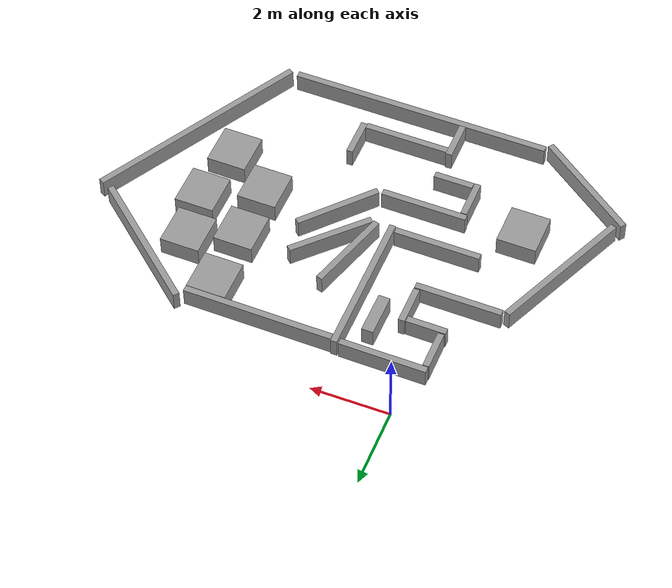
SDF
<?xml version='1.0'?>
<sdf version='1.6'>
  <model name='ws18_amr_master'>
    <link name='link_0'>
      <pose frame=''>-0.315045 -1.91588 -0 0 -0 0</pose>
      <inertial>
        <mass>0.0824965</mass>
        <inertia>
          <ixx>0.00863488</ixx>
          <ixy>0</ixy>
          <ixz>0</ixz>
          <iyy>0.0019429</iyy>
          <iyz>0</iyz>
          <izz>0.00705746</izz>
        </inertia>
        <pose frame=''>0 0 0 0 -0 0</pose>
      </inertial>
      <self_collide>0</self_collide>
      <kinematic>0</kinematic>
      <visual name='visual'>
        <pose frame=''>0 0 0 0 -0 0</pose>
        <geometry>
          <box>
            <size>0.163038 1 0.505999</size>
          </box>
        </geometry>
        <material>
          <lighting>1</lighting>
          <script>
            <uri>file://media/materials/scripts/gazebo.material</uri>
            <name>Gazebo/Grey</name>
          </script>
          <ambient>0.3 0.3 0.3 1</ambient>
          <diffuse>0.7 0.7 0.7 1</diffuse>
          <specular>0.01 0.01 0.01 1</specular>
          <emissive>0 0 0 1</emissive>
        </material>
        <cast_shadows>1</cast_shadows>
        <transparency>0</transparency>
      </visual>
      <collision name='collision'>
        <laser_retro>0</laser_retro>
        <max_contacts>10</max_contacts>
        <pose frame=''>0 0 0 0 -0 0</pose>
        <geometry>
          <box>
            <size>0.163038 1 0.505999</size>
          </box>
        </geometry>
        <surface>
          <friction>
            <ode>
              <mu>1</mu>
              <mu2>1</mu2>
              <fdir1>0 0 0</fdir1>
              <slip1>0</slip1>
              <slip2>0</slip2>
            </ode>
            <torsional>
              <coefficient>1</coefficient>
              <patch_radius>0</patch_radius>
              <surface_radius>0</surface_radius>
              <use_patch_radius>1</use_patch_radius>
              <ode>
                <slip>0</slip>
              </ode>
            </torsional>
          </friction>
          <bounce>
            <restitution_coefficient>0</restitution_coefficient>
            <threshold>1e+06</threshold>
          </bounce>
          <contact>
            <collide_without_contact>0</collide_without_contact>
            <collide_without_contact_bitmask>1</collide_without_contact_bitmask>
            <collide_bitmask>1</collide_bitmask>
            <ode>
              <soft_cfm>0</soft_cfm>
              <soft_erp>0.2</soft_erp>
              <kp>1e+13</kp>
              <kd>1</kd>
              <max_vel>0.01</max_vel>
              <min_depth>0</min_depth>
            </ode>
            <bullet>
              <split_impulse>1</split_impulse>
              <split_impulse_penetration_threshold>-0.01</split_impulse_penetration_threshold>
              <soft_cfm>0</soft_cfm>
              <soft_erp>0.2</soft_erp>
              <kp>1e+13</kp>
              <kd>1</kd>
            </bullet>
          </contact>
        </surface>
      </collision>
    </link>
    <link name='link_0_clone'>
      <pose frame=''>0.710611 -1.33183 0.001064 0 0.012172 1.55915</pose>
      <inertial>
        <mass>0.180006</mass>
        <inertia>
          <ixx>0.0752589</ixx>
          <ixy>0</ixy>
          <ixz>0</ixz>
          <iyy>0.00423938</iyy>
          <iyz>0</iyz>
          <izz>0.071817</izz>
        </inertia>
        <pose frame=''>0 0 0 0 -0 0</pose>
      </inertial>
      <self_collide>0</self_collide>
      <kinematic>0</kinematic>
      <visual name='visual'>
        <pose frame=''>0 0 0 0 -0 0</pose>
        <geometry>
          <box>
            <size>0.163038 2.18199 0.505999</size>
          </box>
        </geometry>
        <material>
          <lighting>1</lighting>
          <script>
            <uri>file://media/materials/scripts/gazebo.material</uri>
            <name>Gazebo/Grey</name>
          </script>
          <ambient>0.3 0.3 0.3 1</ambient>
          <diffuse>0.7 0.7 0.7 1</diffuse>
          <specular>0.01 0.01 0.01 1</specular>
          <emissive>0 0 0 1</emissive>
          <shader type='pixel'/>
        </material>
        <cast_shadows>1</cast_shadows>
        <transparency>0</transparency>
      </visual>
      <collision name='collision'>
        <laser_retro>0</laser_retro>
        <max_contacts>10</max_contacts>
        <pose frame=''>0 0 0 0 -0 0</pose>
        <geometry>
          <box>
            <size>0.163038 2.18199 0.505999</size>
          </box>
        </geometry>
        <surface>
          <friction>
            <ode>
              <mu>1</mu>
              <mu2>1</mu2>
              <fdir1>0 0 0</fdir1>
              <slip1>0</slip1>
              <slip2>0</slip2>
            </ode>
            <torsional>
              <coefficient>1</coefficient>
              <patch_radius>0</patch_radius>
              <surface_radius>0</surface_radius>
              <use_patch_radius>1</use_patch_radius>
              <ode>
                <slip>0</slip>
              </ode>
            </torsional>
          </friction>
          <bounce>
            <restitution_coefficient>0</restitution_coefficient>
            <threshold>1e+06</threshold>
          </bounce>
          <contact>
            <collide_without_contact>0</collide_without_contact>
            <collide_without_contact_bitmask>1</collide_without_contact_bitmask>
            <collide_bitmask>1</collide_bitmask>
            <ode>
              <soft_cfm>0</soft_cfm>
              <soft_erp>0.2</soft_erp>
              <kp>1e+13</kp>
              <kd>1</kd>
              <max_vel>0.01</max_vel>
              <min_depth>0</min_depth>
            </ode>
            <bullet>
              <split_impulse>1</split_impulse>
              <split_impulse_penetration_threshold>-0.01</split_impulse_penetration_threshold>
              <soft_cfm>0</soft_cfm>
              <soft_erp>0.2</soft_erp>
              <kp>1e+13</kp>
              <kd>1</kd>
            </bullet>
          </contact>
        </surface>
      </collision>
    </link>
    <link name='link_0_clone_0'>
      <pose frame=''>0.685279 -2.9377 -0 0 -0 0</pose>
      <inertial>
        <mass>0.0824965</mass>
        <inertia>
          <ixx>0.00863488</ixx>
          <ixy>0</ixy>
          <ixz>0</ixz>
          <iyy>0.0019429</iyy>
          <iyz>0</iyz>
          <izz>0.00705746</izz>
        </inertia>
        <pose frame=''>0 0 0 0 -0 0</pose>
      </inertial>
      <self_collide>0</self_collide>
      <kinematic>0</kinematic>
      <visual name='visual'>
        <pose frame=''>0 0 0 0 -0 0</pose>
        <geometry>
          <box>
            <size>0.163038 1 0.505999</size>
          </box>
        </geometry>
        <material>
          <lighting>1</lighting>
          <script>
            <uri>file://media/materials/scripts/gazebo.material</uri>
            <name>Gazebo/Grey</name>
          </script>
          <ambient>0.3 0.3 0.3 1</ambient>
          <diffuse>0.7 0.7 0.7 1</diffuse>
          <specular>0.01 0.01 0.01 1</specular>
          <emissive>0 0 0 1</emissive>
          <shader type='pixel'/>
        </material>
        <cast_shadows>1</cast_shadows>
        <transparency>0</transparency>
      </visual>
      <collision name='collision'>
        <laser_retro>0</laser_retro>
        <max_contacts>10</max_contacts>
        <pose frame=''>0 0 0 0 -0 0</pose>
        <geometry>
          <box>
            <size>0.163038 1 0.505999</size>
          </box>
        </geometry>
        <surface>
          <friction>
            <ode>
              <mu>1</mu>
              <mu2>1</mu2>
              <fdir1>0 0 0</fdir1>
              <slip1>0</slip1>
              <slip2>0</slip2>
            </ode>
            <torsional>
              <coefficient>1</coefficient>
              <patch_radius>0</patch_radius>
              <surface_radius>0</surface_radius>
              <use_patch_radius>1</use_patch_radius>
              <ode>
                <slip>0</slip>
              </ode>
            </torsional>
          </friction>
          <bounce>
            <restitution_coefficient>0</restitution_coefficient>
            <threshold>1e+06</threshold>
          </bounce>
          <contact>
            <collide_without_contact>0</collide_without_contact>
            <collide_without_contact_bitmask>1</collide_without_contact_bitmask>
            <collide_bitmask>1</collide_bitmask>
            <ode>
              <soft_cfm>0</soft_cfm>
              <soft_erp>0.2</soft_erp>
              <kp>1e+13</kp>
              <kd>1</kd>
              <max_vel>0.01</max_vel>
              <min_depth>0</min_depth>
            </ode>
            <bullet>
              <split_impulse>1</split_impulse>
              <split_impulse_penetration_threshold>-0.01</split_impulse_penetration_threshold>
              <soft_cfm>0</soft_cfm>
              <soft_erp>0.2</soft_erp>
              <kp>1e+13</kp>
              <kd>1</kd>
            </bullet>
          </contact>
        </surface>
      </collision>
    </link>
    <link name='link_0_clone_1'>
      <pose frame=''>1.92532 -3.16382 -0 0 -0 0</pose>
      <inertial>
        <mass>0.311198</mass>
        <inertia>
          <ixx>0.375669</ixx>
          <ixy>0</ixy>
          <ixz>0</ixz>
          <iyy>0.00732913</iyy>
          <iyz>0</iyz>
          <izz>0.369718</izz>
        </inertia>
        <pose frame=''>0 0 0 0 -0 0</pose>
      </inertial>
      <self_collide>0</self_collide>
      <kinematic>0</kinematic>
      <visual name='visual'>
        <pose frame=''>0 0 0 0 -0 0</pose>
        <geometry>
          <box>
            <size>0.163038 3.77227 0.505999</size>
          </box>
        </geometry>
        <material>
          <lighting>1</lighting>
          <script>
            <uri>file://media/materials/scripts/gazebo.material</uri>
            <name>Gazebo/Grey</name>
          </script>
          <ambient>0.3 0.3 0.3 1</ambient>
          <diffuse>0.7 0.7 0.7 1</diffuse>
          <specular>0.01 0.01 0.01 1</specular>
          <emissive>0 0 0 1</emissive>
          <shader type='pixel'/>
        </material>
        <cast_shadows>1</cast_shadows>
        <transparency>0</transparency>
      </visual>
      <collision name='collision'>
        <laser_retro>0</laser_retro>
        <max_contacts>10</max_contacts>
        <pose frame=''>0 0 0 0 -0 0</pose>
        <geometry>
          <box>
            <size>0.163038 3.77227 0.505999</size>
          </box>
        </geometry>
        <surface>
          <friction>
            <ode>
              <mu>1</mu>
              <mu2>1</mu2>
              <fdir1>0 0 0</fdir1>
              <slip1>0</slip1>
              <slip2>0</slip2>
            </ode>
            <torsional>
              <coefficient>1</coefficient>
              <patch_radius>0</patch_radius>
              <surface_radius>0</surface_radius>
              <use_patch_radius>1</use_patch_radius>
              <ode>
                <slip>0</slip>
              </ode>
            </torsional>
          </friction>
          <bounce>
            <restitution_coefficient>0</restitution_coefficient>
            <threshold>1e+06</threshold>
          </bounce>
          <contact>
            <collide_without_contact>0</collide_without_contact>
            <collide_without_contact_bitmask>1</collide_without_contact_bitmask>
            <collide_bitmask>1</collide_bitmask>
            <ode>
              <soft_cfm>0</soft_cfm>
              <soft_erp>0.2</soft_erp>
              <kp>1e+13</kp>
              <kd>1</kd>
              <max_vel>0.01</max_vel>
              <min_depth>0</min_depth>
            </ode>
            <bullet>
              <split_impulse>1</split_impulse>
              <split_impulse_penetration_threshold>-0.01</split_impulse_penetration_threshold>
              <soft_cfm>0</soft_cfm>
              <soft_erp>0.2</soft_erp>
              <kp>1e+13</kp>
              <kd>1</kd>
            </bullet>
          </contact>
        </surface>
      </collision>
    </link>
    <link name='link_0_clone_1_clone'>
      <pose frame=''>-2.27947 -5.2883 -0 -0 -0 -0.406594</pose>
      <inertial>
        <mass>0.311198</mass>
        <inertia>
          <ixx>0.375669</ixx>
          <ixy>0</ixy>
          <ixz>0</ixz>
          <iyy>0.00732913</iyy>
          <iyz>0</iyz>
          <izz>0.369718</izz>
        </inertia>
        <pose frame=''>0 0 0 0 -0 0</pose>
      </inertial>
      <self_collide>0</self_collide>
      <kinematic>0</kinematic>
      <visual name='visual'>
        <pose frame=''>0 0 0 0 -0 0</pose>
        <geometry>
          <box>
            <size>0.163038 3.77227 0.505999</size>
          </box>
        </geometry>
        <material>
          <lighting>1</lighting>
          <script>
            <uri>file://media/materials/scripts/gazebo.material</uri>
            <name>Gazebo/Grey</name>
          </script>
          <ambient>0.3 0.3 0.3 1</ambient>
          <diffuse>0.7 0.7 0.7 1</diffuse>
          <specular>0.01 0.01 0.01 1</specular>
          <emissive>0 0 0 1</emissive>
          <shader type='pixel'/>
        </material>
        <cast_shadows>1</cast_shadows>
        <transparency>0</transparency>
      </visual>
      <collision name='collision'>
        <laser_retro>0</laser_retro>
        <max_contacts>10</max_contacts>
        <pose frame=''>0 0 0 0 -0 0</pose>
        <geometry>
          <box>
            <size>0.163038 3.77227 0.505999</size>
          </box>
        </geometry>
        <surface>
          <friction>
            <ode>
              <mu>1</mu>
              <mu2>1</mu2>
              <fdir1>0 0 0</fdir1>
              <slip1>0</slip1>
              <slip2>0</slip2>
            </ode>
            <torsional>
              <coefficient>1</coefficient>
              <patch_radius>0</patch_radius>
              <surface_radius>0</surface_radius>
              <use_patch_radius>1</use_patch_radius>
              <ode>
                <slip>0</slip>
              </ode>
            </torsional>
          </friction>
          <bounce>
            <restitution_coefficient>0</restitution_coefficient>
            <threshold>1e+06</threshold>
          </bounce>
          <contact>
            <collide_without_contact>0</collide_without_contact>
            <collide_without_contact_bitmask>1</collide_without_contact_bitmask>
            <collide_bitmask>1</collide_bitmask>
            <ode>
              <soft_cfm>0</soft_cfm>
              <soft_erp>0.2</soft_erp>
              <kp>1e+13</kp>
              <kd>1</kd>
              <max_vel>0.01</max_vel>
              <min_depth>0</min_depth>
            </ode>
            <bullet>
              <split_impulse>1</split_impulse>
              <split_impulse_penetration_threshold>-0.01</split_impulse_penetration_threshold>
              <soft_cfm>0</soft_cfm>
              <soft_erp>0.2</soft_erp>
              <kp>1e+13</kp>
              <kd>1</kd>
            </bullet>
          </contact>
        </surface>
      </collision>
    </link>
    <link name='link_0_clone_1_clone_clone'>
      <pose frame=''>-2.0016 -8.01046 -0 0 0 -2.2011</pose>
      <inertial>
        <mass>0.252342</mass>
        <inertia>
          <ixx>0.202136</ixx>
          <ixy>0</ixy>
          <ixz>0</ixz>
          <iyy>0.005943</iyy>
          <iyz>0</iyz>
          <izz>0.197311</izz>
        </inertia>
        <pose frame=''>0 0 0 0 -0 0</pose>
      </inertial>
      <self_collide>0</self_collide>
      <kinematic>0</kinematic>
      <visual name='visual'>
        <pose frame=''>0 0 0 0 -0 0</pose>
        <geometry>
          <box>
            <size>0.163038 3.05883 0.505999</size>
          </box>
        </geometry>
        <material>
          <lighting>1</lighting>
          <script>
            <uri>file://media/materials/scripts/gazebo.material</uri>
            <name>Gazebo/Grey</name>
          </script>
          <ambient>0.3 0.3 0.3 1</ambient>
          <diffuse>0.7 0.7 0.7 1</diffuse>
          <specular>0.01 0.01 0.01 1</specular>
          <emissive>0 0 0 1</emissive>
          <shader type='pixel'/>
        </material>
        <cast_shadows>1</cast_shadows>
        <transparency>0</transparency>
      </visual>
      <collision name='collision'>
        <laser_retro>0</laser_retro>
        <max_contacts>10</max_contacts>
        <pose frame=''>0 0 0 0 -0 0</pose>
        <geometry>
          <box>
            <size>0.163038 3.05883 0.505999</size>
          </box>
        </geometry>
        <surface>
          <friction>
            <ode>
              <mu>1</mu>
              <mu2>1</mu2>
              <fdir1>0 0 0</fdir1>
              <slip1>0</slip1>
              <slip2>0</slip2>
            </ode>
            <torsional>
              <coefficient>1</coefficient>
              <patch_radius>0</patch_radius>
              <surface_radius>0</surface_radius>
              <use_patch_radius>1</use_patch_radius>
              <ode>
                <slip>0</slip>
              </ode>
            </torsional>
          </friction>
          <bounce>
            <restitution_coefficient>0</restitution_coefficient>
            <threshold>1e+06</threshold>
          </bounce>
          <contact>
            <collide_without_contact>0</collide_without_contact>
            <collide_without_contact_bitmask>1</collide_without_contact_bitmask>
            <collide_bitmask>1</collide_bitmask>
            <ode>
              <soft_cfm>0</soft_cfm>
              <soft_erp>0.2</soft_erp>
              <kp>1e+13</kp>
              <kd>1</kd>
              <max_vel>0.01</max_vel>
              <min_depth>0</min_depth>
            </ode>
            <bullet>
              <split_impulse>1</split_impulse>
              <split_impulse_penetration_threshold>-0.01</split_impulse_penetration_threshold>
              <soft_cfm>0</soft_cfm>
              <soft_erp>0.2</soft_erp>
              <kp>1e+13</kp>
              <kd>1</kd>
            </bullet>
          </contact>
        </surface>
      </collision>
    </link>
    <link name='link_0_clone_1_clone_clone_0'>
      <pose frame=''>7.62136 -6.28425 -0 -0 -0 -0.508443</pose>
      <inertial>
        <mass>0.4862</mass>
        <inertia>
          <ixx>1.4177</ixx>
          <ixy>0</ixy>
          <ixz>0</ixz>
          <iyy>0.0114507</iyy>
          <iyz>0</iyz>
          <izz>1.40841</izz>
        </inertia>
        <pose frame=''>0 0 0 0 -0 0</pose>
      </inertial>
      <self_collide>0</self_collide>
      <kinematic>0</kinematic>
      <visual name='visual'>
        <pose frame=''>0 0 0 0 -0 0</pose>
        <geometry>
          <box>
            <size>0.163038 5.89361 0.505999</size>
          </box>
        </geometry>
        <material>
          <lighting>1</lighting>
          <script>
            <uri>file://media/materials/scripts/gazebo.material</uri>
            <name>Gazebo/Grey</name>
          </script>
          <ambient>0.3 0.3 0.3 1</ambient>
          <diffuse>0.7 0.7 0.7 1</diffuse>
          <specular>0.01 0.01 0.01 1</specular>
          <emissive>0 0 0 1</emissive>
          <shader type='pixel'/>
        </material>
        <cast_shadows>1</cast_shadows>
        <transparency>0</transparency>
      </visual>
      <collision name='collision'>
        <laser_retro>0</laser_retro>
        <max_contacts>10</max_contacts>
        <pose frame=''>0 0 0 0 -0 0</pose>
        <geometry>
          <box>
            <size>0.163038 5.89361 0.505999</size>
          </box>
        </geometry>
        <surface>
          <friction>
            <ode>
              <mu>1</mu>
              <mu2>1</mu2>
              <fdir1>0 0 0</fdir1>
              <slip1>0</slip1>
              <slip2>0</slip2>
            </ode>
            <torsional>
              <coefficient>1</coefficient>
              <patch_radius>0</patch_radius>
              <surface_radius>0</surface_radius>
              <use_patch_radius>1</use_patch_radius>
              <ode>
                <slip>0</slip>
              </ode>
            </torsional>
          </friction>
          <bounce>
            <restitution_coefficient>0</restitution_coefficient>
            <threshold>1e+06</threshold>
          </bounce>
          <contact>
            <collide_without_contact>0</collide_without_contact>
            <collide_without_contact_bitmask>1</collide_without_contact_bitmask>
            <collide_bitmask>1</collide_bitmask>
            <ode>
              <soft_cfm>0</soft_cfm>
              <soft_erp>0.2</soft_erp>
              <kp>1e+13</kp>
              <kd>1</kd>
              <max_vel>0.01</max_vel>
              <min_depth>0</min_depth>
            </ode>
            <bullet>
              <split_impulse>1</split_impulse>
              <split_impulse_penetration_threshold>-0.01</split_impulse_penetration_threshold>
              <soft_cfm>0</soft_cfm>
              <soft_erp>0.2</soft_erp>
              <kp>1e+13</kp>
              <kd>1</kd>
            </bullet>
          </contact>
        </surface>
      </collision>
    </link>
    <link name='link_0_clone_1_clone_clone_clone'>
      <pose frame=''>7.32668 -2.40651 -0 0 0 -2.27698</pose>
      <inertial>
        <mass>0.311198</mass>
        <inertia>
          <ixx>0.375669</ixx>
          <ixy>0</ixy>
          <ixz>0</ixz>
          <iyy>0.00732913</iyy>
          <iyz>0</iyz>
          <izz>0.369718</izz>
        </inertia>
        <pose frame=''>0 0 0 0 -0 0</pose>
      </inertial>
      <self_collide>0</self_collide>
      <kinematic>0</kinematic>
      <visual name='visual'>
        <pose frame=''>0 0 0 0 -0 0</pose>
        <geometry>
          <box>
            <size>0.163038 3.77227 0.505999</size>
          </box>
        </geometry>
        <material>
          <lighting>1</lighting>
          <script>
            <uri>file://media/materials/scripts/gazebo.material</uri>
            <name>Gazebo/Grey</name>
          </script>
          <ambient>0.3 0.3 0.3 1</ambient>
          <diffuse>0.7 0.7 0.7 1</diffuse>
          <specular>0.01 0.01 0.01 1</specular>
          <emissive>0 0 0 1</emissive>
          <shader type='pixel'/>
        </material>
        <cast_shadows>1</cast_shadows>
        <transparency>0</transparency>
      </visual>
      <collision name='collision'>
        <laser_retro>0</laser_retro>
        <max_contacts>10</max_contacts>
        <pose frame=''>0 0 0 0 -0 0</pose>
        <geometry>
          <box>
            <size>0.163038 3.77227 0.505999</size>
          </box>
        </geometry>
        <surface>
          <friction>
            <ode>
              <mu>1</mu>
              <mu2>1</mu2>
              <fdir1>0 0 0</fdir1>
              <slip1>0</slip1>
              <slip2>0</slip2>
            </ode>
            <torsional>
              <coefficient>1</coefficient>
              <patch_radius>0</patch_radius>
              <surface_radius>0</surface_radius>
              <use_patch_radius>1</use_patch_radius>
              <ode>
                <slip>0</slip>
              </ode>
            </torsional>
          </friction>
          <bounce>
            <restitution_coefficient>0</restitution_coefficient>
            <threshold>1e+06</threshold>
          </bounce>
          <contact>
            <collide_without_contact>0</collide_without_contact>
            <collide_without_contact_bitmask>1</collide_without_contact_bitmask>
            <collide_bitmask>1</collide_bitmask>
            <ode>
              <soft_cfm>0</soft_cfm>
              <soft_erp>0.2</soft_erp>
              <kp>1e+13</kp>
              <kd>1</kd>
              <max_vel>0.01</max_vel>
              <min_depth>0</min_depth>
            </ode>
            <bullet>
              <split_impulse>1</split_impulse>
              <split_impulse_penetration_threshold>-0.01</split_impulse_penetration_threshold>
              <soft_cfm>0</soft_cfm>
              <soft_erp>0.2</soft_erp>
              <kp>1e+13</kp>
              <kd>1</kd>
            </bullet>
          </contact>
        </surface>
      </collision>
    </link>
    <link name='link_0_clone_2'>
      <pose frame=''>0.470275 -6.53761 -0 0 -0 0</pose>
      <inertial>
        <mass>0.0824965</mass>
        <inertia>
          <ixx>0.00863488</ixx>
          <ixy>0</ixy>
          <ixz>0</ixz>
          <iyy>0.0019429</iyy>
          <iyz>0</iyz>
          <izz>0.00705746</izz>
        </inertia>
        <pose frame=''>0 0 0 0 -0 0</pose>
      </inertial>
      <self_collide>0</self_collide>
      <kinematic>0</kinematic>
      <visual name='visual'>
        <pose frame=''>0 0 0 0 -0 0</pose>
        <geometry>
          <box>
            <size>0.163038 1 0.505999</size>
          </box>
        </geometry>
        <material>
          <lighting>1</lighting>
          <script>
            <uri>file://media/materials/scripts/gazebo.material</uri>
            <name>Gazebo/Grey</name>
          </script>
          <ambient>0.3 0.3 0.3 1</ambient>
          <diffuse>0.7 0.7 0.7 1</diffuse>
          <specular>0.01 0.01 0.01 1</specular>
          <emissive>0 0 0 1</emissive>
          <shader type='pixel'/>
        </material>
        <cast_shadows>1</cast_shadows>
        <transparency>0</transparency>
      </visual>
      <collision name='collision'>
        <laser_retro>0</laser_retro>
        <max_contacts>10</max_contacts>
        <pose frame=''>0 0 0 0 -0 0</pose>
        <geometry>
          <box>
            <size>0.163038 1 0.505999</size>
          </box>
        </geometry>
        <surface>
          <friction>
            <ode>
              <mu>1</mu>
              <mu2>1</mu2>
              <fdir1>0 0 0</fdir1>
              <slip1>0</slip1>
              <slip2>0</slip2>
            </ode>
            <torsional>
              <coefficient>1</coefficient>
              <patch_radius>0</patch_radius>
              <surface_radius>0</surface_radius>
              <use_patch_radius>1</use_patch_radius>
              <ode>
                <slip>0</slip>
              </ode>
            </torsional>
          </friction>
          <bounce>
            <restitution_coefficient>0</restitution_coefficient>
            <threshold>1e+06</threshold>
          </bounce>
          <contact>
            <collide_without_contact>0</collide_without_contact>
            <collide_without_contact_bitmask>1</collide_without_contact_bitmask>
            <collide_bitmask>1</collide_bitmask>
            <ode>
              <soft_cfm>0</soft_cfm>
              <soft_erp>0.2</soft_erp>
              <kp>1e+13</kp>
              <kd>1</kd>
              <max_vel>0.01</max_vel>
              <min_depth>0</min_depth>
            </ode>
            <bullet>
              <split_impulse>1</split_impulse>
              <split_impulse_penetration_threshold>-0.01</split_impulse_penetration_threshold>
              <soft_cfm>0</soft_cfm>
              <soft_erp>0.2</soft_erp>
              <kp>1e+13</kp>
              <kd>1</kd>
            </bullet>
          </contact>
        </surface>
      </collision>
    </link>
    <link name='link_0_clone_2_clone'>
      <pose frame=''>1.4792 -8.1933 -0 0 -0 0</pose>
      <inertial>
        <mass>0.0824965</mass>
        <inertia>
          <ixx>0.00863488</ixx>
          <ixy>0</ixy>
          <ixz>0</ixz>
          <iyy>0.0019429</iyy>
          <iyz>0</iyz>
          <izz>0.00705746</izz>
        </inertia>
        <pose frame=''>0 0 0 0 -0 0</pose>
      </inertial>
      <self_collide>0</self_collide>
      <kinematic>0</kinematic>
      <visual name='visual'>
        <pose frame=''>0 0 0 0 -0 0</pose>
        <geometry>
          <box>
            <size>0.163038 1 0.505999</size>
          </box>
        </geometry>
        <material>
          <lighting>1</lighting>
          <script>
            <uri>file://media/materials/scripts/gazebo.material</uri>
            <name>Gazebo/Grey</name>
          </script>
          <ambient>0.3 0.3 0.3 1</ambient>
          <diffuse>0.7 0.7 0.7 1</diffuse>
          <specular>0.01 0.01 0.01 1</specular>
          <emissive>0 0 0 1</emissive>
          <shader type='pixel'/>
        </material>
        <cast_shadows>1</cast_shadows>
        <transparency>0</transparency>
      </visual>
      <collision name='collision'>
        <laser_retro>0</laser_retro>
        <max_contacts>10</max_contacts>
        <pose frame=''>0 0 0 0 -0 0</pose>
        <geometry>
          <box>
            <size>0.163038 1 0.505999</size>
          </box>
        </geometry>
        <surface>
          <friction>
            <ode>
              <mu>1</mu>
              <mu2>1</mu2>
              <fdir1>0 0 0</fdir1>
              <slip1>0</slip1>
              <slip2>0</slip2>
            </ode>
            <torsional>
              <coefficient>1</coefficient>
              <patch_radius>0</patch_radius>
              <surface_radius>0</surface_radius>
              <use_patch_radius>1</use_patch_radius>
              <ode>
                <slip>0</slip>
              </ode>
            </torsional>
          </friction>
          <bounce>
            <restitution_coefficient>0</restitution_coefficient>
            <threshold>1e+06</threshold>
          </bounce>
          <contact>
            <collide_without_contact>0</collide_without_contact>
            <collide_without_contact_bitmask>1</collide_without_contact_bitmask>
            <collide_bitmask>1</collide_bitmask>
            <ode>
              <soft_cfm>0</soft_cfm>
              <soft_erp>0.2</soft_erp>
              <kp>1e+13</kp>
              <kd>1</kd>
              <max_vel>0.01</max_vel>
              <min_depth>0</min_depth>
            </ode>
            <bullet>
              <split_impulse>1</split_impulse>
              <split_impulse_penetration_threshold>-0.01</split_impulse_penetration_threshold>
              <soft_cfm>0</soft_cfm>
              <soft_erp>0.2</soft_erp>
              <kp>1e+13</kp>
              <kd>1</kd>
            </bullet>
          </contact>
        </surface>
      </collision>
    </link>
    <link name='link_0_clone_2_clone_0'>
      <pose frame=''>3.79092 -7.37969 -0 0 -0 0</pose>
      <inertial>
        <mass>0.0824965</mass>
        <inertia>
          <ixx>0.00863488</ixx>
          <ixy>0</ixy>
          <ixz>0</ixz>
          <iyy>0.0019429</iyy>
          <iyz>0</iyz>
          <izz>0.00705746</izz>
        </inertia>
        <pose frame=''>0 0 0 0 -0 0</pose>
      </inertial>
      <self_collide>0</self_collide>
      <kinematic>0</kinematic>
      <visual name='visual'>
        <pose frame=''>0 0 0 0 -0 0</pose>
        <geometry>
          <box>
            <size>0.163038 1 0.505999</size>
          </box>
        </geometry>
        <material>
          <lighting>1</lighting>
          <script>
            <uri>file://media/materials/scripts/gazebo.material</uri>
            <name>Gazebo/Grey</name>
          </script>
          <ambient>0.3 0.3 0.3 1</ambient>
          <diffuse>0.7 0.7 0.7 1</diffuse>
          <specular>0.01 0.01 0.01 1</specular>
          <emissive>0 0 0 1</emissive>
          <shader type='pixel'/>
        </material>
        <cast_shadows>1</cast_shadows>
        <transparency>0</transparency>
      </visual>
      <collision name='collision'>
        <laser_retro>0</laser_retro>
        <max_contacts>10</max_contacts>
        <pose frame=''>0 0 0 0 -0 0</pose>
        <geometry>
          <box>
            <size>0.163038 1 0.505999</size>
          </box>
        </geometry>
        <surface>
          <friction>
            <ode>
              <mu>1</mu>
              <mu2>1</mu2>
              <fdir1>0 0 0</fdir1>
              <slip1>0</slip1>
              <slip2>0</slip2>
            </ode>
            <torsional>
              <coefficient>1</coefficient>
              <patch_radius>0</patch_radius>
              <surface_radius>0</surface_radius>
              <use_patch_radius>1</use_patch_radius>
              <ode>
                <slip>0</slip>
              </ode>
            </torsional>
          </friction>
          <bounce>
            <restitution_coefficient>0</restitution_coefficient>
            <threshold>1e+06</threshold>
          </bounce>
          <contact>
            <collide_without_contact>0</collide_without_contact>
            <collide_without_contact_bitmask>1</collide_without_contact_bitmask>
            <collide_bitmask>1</collide_bitmask>
            <ode>
              <soft_cfm>0</soft_cfm>
              <soft_erp>0.2</soft_erp>
              <kp>1e+13</kp>
              <kd>1</kd>
              <max_vel>0.01</max_vel>
              <min_depth>0</min_depth>
            </ode>
            <bullet>
              <split_impulse>1</split_impulse>
              <split_impulse_penetration_threshold>-0.01</split_impulse_penetration_threshold>
              <soft_cfm>0</soft_cfm>
              <soft_erp>0.2</soft_erp>
              <kp>1e+13</kp>
              <kd>1</kd>
            </bullet>
          </contact>
        </surface>
      </collision>
    </link>
    <link name='link_0_clone_clone'>
      <pose frame=''>0.080109 -2.51757 0.018209 0 0.012172 1.55915</pose>
      <inertial>
        <mass>0.0824965</mass>
        <inertia>
          <ixx>0.00863488</ixx>
          <ixy>0</ixy>
          <ixz>0</ixz>
          <iyy>0.0019429</iyy>
          <iyz>0</iyz>
          <izz>0.00705746</izz>
        </inertia>
        <pose frame=''>0 0 0 0 -0 0</pose>
      </inertial>
      <self_collide>0</self_collide>
      <kinematic>0</kinematic>
      <visual name='visual'>
        <pose frame=''>0 0 0 0 -0 0</pose>
        <geometry>
          <box>
            <size>0.163038 1 0.505999</size>
          </box>
        </geometry>
        <material>
          <lighting>1</lighting>
          <script>
            <uri>file://media/materials/scripts/gazebo.material</uri>
            <name>Gazebo/Grey</name>
          </script>
          <ambient>0.3 0.3 0.3 1</ambient>
          <diffuse>0.7 0.7 0.7 1</diffuse>
          <specular>0.01 0.01 0.01 1</specular>
          <emissive>0 0 0 1</emissive>
          <shader type='pixel'/>
        </material>
        <cast_shadows>1</cast_shadows>
        <transparency>0</transparency>
      </visual>
      <collision name='collision'>
        <laser_retro>0</laser_retro>
        <max_contacts>10</max_contacts>
        <pose frame=''>0 0 0 0 -0 0</pose>
        <geometry>
          <box>
            <size>0.163038 1 0.505999</size>
          </box>
        </geometry>
        <surface>
          <friction>
            <ode>
              <mu>1</mu>
              <mu2>1</mu2>
              <fdir1>0 0 0</fdir1>
              <slip1>0</slip1>
              <slip2>0</slip2>
            </ode>
            <torsional>
              <coefficient>1</coefficient>
              <patch_radius>0</patch_radius>
              <surface_radius>0</surface_radius>
              <use_patch_radius>1</use_patch_radius>
              <ode>
                <slip>0</slip>
              </ode>
            </torsional>
          </friction>
          <bounce>
            <restitution_coefficient>0</restitution_coefficient>
            <threshold>1e+06</threshold>
          </bounce>
          <contact>
            <collide_without_contact>0</collide_without_contact>
            <collide_without_contact_bitmask>1</collide_without_contact_bitmask>
            <collide_bitmask>1</collide_bitmask>
            <ode>
              <soft_cfm>0</soft_cfm>
              <soft_erp>0.2</soft_erp>
              <kp>1e+13</kp>
              <kd>1</kd>
              <max_vel>0.01</max_vel>
              <min_depth>0</min_depth>
            </ode>
            <bullet>
              <split_impulse>1</split_impulse>
              <split_impulse_penetration_threshold>-0.01</split_impulse_penetration_threshold>
              <soft_cfm>0</soft_cfm>
              <soft_erp>0.2</soft_erp>
              <kp>1e+13</kp>
              <kd>1</kd>
            </bullet>
          </contact>
        </surface>
      </collision>
    </link>
    <link name='link_0_clone_clone_0'>
      <pose frame=''>-0.33418 -3.53818 0.001064 0 0.012172 1.55915</pose>
      <inertial>
        <mass>0.180006</mass>
        <inertia>
          <ixx>0.0752589</ixx>
          <ixy>0</ixy>
          <ixz>0</ixz>
          <iyy>0.00423938</iyy>
          <iyz>0</iyz>
          <izz>0.071817</izz>
        </inertia>
        <pose frame=''>0 0 0 0 -0 0</pose>
      </inertial>
      <self_collide>0</self_collide>
      <kinematic>0</kinematic>
      <visual name='visual'>
        <pose frame=''>0 0 0 0 -0 0</pose>
        <geometry>
          <box>
            <size>0.163038 2.18199 0.505999</size>
          </box>
        </geometry>
        <material>
          <lighting>1</lighting>
          <script>
            <uri>file://media/materials/scripts/gazebo.material</uri>
            <name>Gazebo/Grey</name>
          </script>
          <ambient>0.3 0.3 0.3 1</ambient>
          <diffuse>0.7 0.7 0.7 1</diffuse>
          <specular>0.01 0.01 0.01 1</specular>
          <emissive>0 0 0 1</emissive>
          <shader type='pixel'/>
        </material>
        <cast_shadows>1</cast_shadows>
        <transparency>0</transparency>
      </visual>
      <collision name='collision'>
        <laser_retro>0</laser_retro>
        <max_contacts>10</max_contacts>
        <pose frame=''>0 0 0 0 -0 0</pose>
        <geometry>
          <box>
            <size>0.163038 2.18199 0.505999</size>
          </box>
        </geometry>
        <surface>
          <friction>
            <ode>
              <mu>1</mu>
              <mu2>1</mu2>
              <fdir1>0 0 0</fdir1>
              <slip1>0</slip1>
              <slip2>0</slip2>
            </ode>
            <torsional>
              <coefficient>1</coefficient>
              <patch_radius>0</patch_radius>
              <surface_radius>0</surface_radius>
              <use_patch_radius>1</use_patch_radius>
              <ode>
                <slip>0</slip>
              </ode>
            </torsional>
          </friction>
          <bounce>
            <restitution_coefficient>0</restitution_coefficient>
            <threshold>1e+06</threshold>
          </bounce>
          <contact>
            <collide_without_contact>0</collide_without_contact>
            <collide_without_contact_bitmask>1</collide_without_contact_bitmask>
            <collide_bitmask>1</collide_bitmask>
            <ode>
              <soft_cfm>0</soft_cfm>
              <soft_erp>0.2</soft_erp>
              <kp>1e+13</kp>
              <kd>1</kd>
              <max_vel>0.01</max_vel>
              <min_depth>0</min_depth>
            </ode>
            <bullet>
              <split_impulse>1</split_impulse>
              <split_impulse_penetration_threshold>-0.01</split_impulse_penetration_threshold>
              <soft_cfm>0</soft_cfm>
              <soft_erp>0.2</soft_erp>
              <kp>1e+13</kp>
              <kd>1</kd>
            </bullet>
          </contact>
        </surface>
      </collision>
    </link>
    <link name='link_0_clone_clone_1'>
      <pose frame=''>0.725389 -4.9345 -8.7e-05 0 0.012172 1.55915</pose>
      <inertial>
        <mass>0.180006</mass>
        <inertia>
          <ixx>0.0752589</ixx>
          <ixy>0</ixy>
          <ixz>0</ixz>
          <iyy>0.00423938</iyy>
          <iyz>0</iyz>
          <izz>0.071817</izz>
        </inertia>
        <pose frame=''>0 0 0 0 -0 0</pose>
      </inertial>
      <self_collide>0</self_collide>
      <kinematic>0</kinematic>
      <visual name='visual'>
        <pose frame=''>0 0 0 0 -0 0</pose>
        <geometry>
          <box>
            <size>0.163038 2.18199 0.505999</size>
          </box>
        </geometry>
        <material>
          <lighting>1</lighting>
          <script>
            <uri>file://media/materials/scripts/gazebo.material</uri>
            <name>Gazebo/Grey</name>
          </script>
          <ambient>0.3 0.3 0.3 1</ambient>
          <diffuse>0.7 0.7 0.7 1</diffuse>
          <specular>0.01 0.01 0.01 1</specular>
          <emissive>0 0 0 1</emissive>
          <shader type='pixel'/>
        </material>
        <cast_shadows>1</cast_shadows>
        <transparency>0</transparency>
      </visual>
      <collision name='collision'>
        <laser_retro>0</laser_retro>
        <max_contacts>10</max_contacts>
        <pose frame=''>0 0 0 0 -0 0</pose>
        <geometry>
          <box>
            <size>0.163038 2.18199 0.505999</size>
          </box>
        </geometry>
        <surface>
          <friction>
            <ode>
              <mu>1</mu>
              <mu2>1</mu2>
              <fdir1>0 0 0</fdir1>
              <slip1>0</slip1>
              <slip2>0</slip2>
            </ode>
            <torsional>
              <coefficient>1</coefficient>
              <patch_radius>0</patch_radius>
              <surface_radius>0</surface_radius>
              <use_patch_radius>1</use_patch_radius>
              <ode>
                <slip>0</slip>
              </ode>
            </torsional>
          </friction>
          <bounce>
            <restitution_coefficient>0</restitution_coefficient>
            <threshold>1e+06</threshold>
          </bounce>
          <contact>
            <collide_without_contact>0</collide_without_contact>
            <collide_without_contact_bitmask>1</collide_without_contact_bitmask>
            <collide_bitmask>1</collide_bitmask>
            <ode>
              <soft_cfm>0</soft_cfm>
              <soft_erp>0.2</soft_erp>
              <kp>1e+13</kp>
              <kd>1</kd>
              <max_vel>0.01</max_vel>
              <min_depth>0</min_depth>
            </ode>
            <bullet>
              <split_impulse>1</split_impulse>
              <split_impulse_penetration_threshold>-0.01</split_impulse_penetration_threshold>
              <soft_cfm>0</soft_cfm>
              <soft_erp>0.2</soft_erp>
              <kp>1e+13</kp>
              <kd>1</kd>
            </bullet>
          </contact>
        </surface>
      </collision>
    </link>
    <link name='link_0_clone_clone_1_clone'>
      <pose frame=''>2.64933 -8.78868 -8.7e-05 0 0.012172 1.55915</pose>
      <inertial>
        <mass>0.549374</mass>
        <inertia>
          <ixx>2.04199</ixx>
          <ixy>0</ixy>
          <ixz>0</ixz>
          <iyy>0.0129385</iyy>
          <iyz>0</iyz>
          <izz>2.03149</izz>
        </inertia>
        <pose frame=''>0 0 0 0 -0 0</pose>
      </inertial>
      <self_collide>0</self_collide>
      <kinematic>0</kinematic>
      <visual name='visual'>
        <pose frame=''>0 0 0 0 -0 0</pose>
        <geometry>
          <box>
            <size>0.163038 6.65939 0.505999</size>
          </box>
        </geometry>
        <material>
          <lighting>1</lighting>
          <script>
            <uri>file://media/materials/scripts/gazebo.material</uri>
            <name>Gazebo/Grey</name>
          </script>
          <ambient>0.3 0.3 0.3 1</ambient>
          <diffuse>0.7 0.7 0.7 1</diffuse>
          <specular>0.01 0.01 0.01 1</specular>
          <emissive>0 0 0 1</emissive>
          <shader type='pixel'/>
        </material>
        <cast_shadows>1</cast_shadows>
        <transparency>0</transparency>
      </visual>
      <collision name='collision'>
        <laser_retro>0</laser_retro>
        <max_contacts>10</max_contacts>
        <pose frame=''>0 0 0 0 -0 0</pose>
        <geometry>
          <box>
            <size>0.163038 6.65939 0.505999</size>
          </box>
        </geometry>
        <surface>
          <friction>
            <ode>
              <mu>1</mu>
              <mu2>1</mu2>
              <fdir1>0 0 0</fdir1>
              <slip1>0</slip1>
              <slip2>0</slip2>
            </ode>
            <torsional>
              <coefficient>1</coefficient>
              <patch_radius>0</patch_radius>
              <surface_radius>0</surface_radius>
              <use_patch_radius>1</use_patch_radius>
              <ode>
                <slip>0</slip>
              </ode>
            </torsional>
          </friction>
          <bounce>
            <restitution_coefficient>0</restitution_coefficient>
            <threshold>1e+06</threshold>
          </bounce>
          <contact>
            <collide_without_contact>0</collide_without_contact>
            <collide_without_contact_bitmask>1</collide_without_contact_bitmask>
            <collide_bitmask>1</collide_bitmask>
            <ode>
              <soft_cfm>0</soft_cfm>
              <soft_erp>0.2</soft_erp>
              <kp>1e+13</kp>
              <kd>1</kd>
              <max_vel>0.01</max_vel>
              <min_depth>0</min_depth>
            </ode>
            <bullet>
              <split_impulse>1</split_impulse>
              <split_impulse_penetration_threshold>-0.01</split_impulse_penetration_threshold>
              <soft_cfm>0</soft_cfm>
              <soft_erp>0.2</soft_erp>
              <kp>1e+13</kp>
              <kd>1</kd>
            </bullet>
          </contact>
        </surface>
      </collision>
    </link>
    <link name='link_0_clone_clone_1_clone_0'>
      <pose frame=''>3.39746 -5.13705 9.6e-05 0.009103 0.00808 2.40401</pose>
      <inertial>
        <mass>0.180006</mass>
        <inertia>
          <ixx>0.0752589</ixx>
          <ixy>0</ixy>
          <ixz>0</ixz>
          <iyy>0.00423938</iyy>
          <iyz>0</iyz>
          <izz>0.071817</izz>
        </inertia>
        <pose frame=''>0 0 0 0 -0 0</pose>
      </inertial>
      <self_collide>0</self_collide>
      <kinematic>0</kinematic>
      <visual name='visual'>
        <pose frame=''>0 0 0 0 -0 0</pose>
        <geometry>
          <box>
            <size>0.163038 2.18199 0.505999</size>
          </box>
        </geometry>
        <material>
          <lighting>1</lighting>
          <script>
            <uri>file://media/materials/scripts/gazebo.material</uri>
            <name>Gazebo/Grey</name>
          </script>
          <ambient>0.3 0.3 0.3 1</ambient>
          <diffuse>0.7 0.7 0.7 1</diffuse>
          <specular>0.01 0.01 0.01 1</specular>
          <emissive>0 0 0 1</emissive>
          <shader type='pixel'/>
        </material>
        <cast_shadows>1</cast_shadows>
        <transparency>0</transparency>
      </visual>
      <collision name='collision'>
        <laser_retro>0</laser_retro>
        <max_contacts>10</max_contacts>
        <pose frame=''>0 0 0 0 -0 0</pose>
        <geometry>
          <box>
            <size>0.163038 2.18199 0.505999</size>
          </box>
        </geometry>
        <surface>
          <friction>
            <ode>
              <mu>1</mu>
              <mu2>1</mu2>
              <fdir1>0 0 0</fdir1>
              <slip1>0</slip1>
              <slip2>0</slip2>
            </ode>
            <torsional>
              <coefficient>1</coefficient>
              <patch_radius>0</patch_radius>
              <surface_radius>0</surface_radius>
              <use_patch_radius>1</use_patch_radius>
              <ode>
                <slip>0</slip>
              </ode>
            </torsional>
          </friction>
          <bounce>
            <restitution_coefficient>0</restitution_coefficient>
            <threshold>1e+06</threshold>
          </bounce>
          <contact>
            <collide_without_contact>0</collide_without_contact>
            <collide_without_contact_bitmask>1</collide_without_contact_bitmask>
            <collide_bitmask>1</collide_bitmask>
            <ode>
              <soft_cfm>0</soft_cfm>
              <soft_erp>0.2</soft_erp>
              <kp>1e+13</kp>
              <kd>1</kd>
              <max_vel>0.01</max_vel>
              <min_depth>0</min_depth>
            </ode>
            <bullet>
              <split_impulse>1</split_impulse>
              <split_impulse_penetration_threshold>-0.01</split_impulse_penetration_threshold>
              <soft_cfm>0</soft_cfm>
              <soft_erp>0.2</soft_erp>
              <kp>1e+13</kp>
              <kd>1</kd>
            </bullet>
          </contact>
        </surface>
      </collision>
    </link>
    <link name='link_0_clone_clone_1_clone_1'>
      <pose frame=''>3.2263 -4.25366 -8.7e-05 0.008831 0.008377 2.37089</pose>
      <inertial>
        <mass>0.180006</mass>
        <inertia>
          <ixx>0.0752589</ixx>
          <ixy>0</ixy>
          <ixz>0</ixz>
          <iyy>0.00423938</iyy>
          <iyz>0</iyz>
          <izz>0.071817</izz>
        </inertia>
        <pose frame=''>0 0 0 0 -0 0</pose>
      </inertial>
      <self_collide>0</self_collide>
      <kinematic>0</kinematic>
      <visual name='visual'>
        <pose frame=''>0 0 0 0 -0 0</pose>
        <geometry>
          <box>
            <size>0.163038 2.18199 0.505999</size>
          </box>
        </geometry>
        <material>
          <lighting>1</lighting>
          <script>
            <uri>file://media/materials/scripts/gazebo.material</uri>
            <name>Gazebo/Grey</name>
          </script>
          <ambient>0.3 0.3 0.3 1</ambient>
          <diffuse>0.7 0.7 0.7 1</diffuse>
          <specular>0.01 0.01 0.01 1</specular>
          <emissive>0 0 0 1</emissive>
          <shader type='pixel'>
            <normal_map>__default__</normal_map>
          </shader>
        </material>
        <cast_shadows>1</cast_shadows>
        <transparency>0</transparency>
      </visual>
      <collision name='collision'>
        <laser_retro>0</laser_retro>
        <max_contacts>10</max_contacts>
        <pose frame=''>0 0 0 0 -0 0</pose>
        <geometry>
          <box>
            <size>0.163038 2.18199 0.505999</size>
          </box>
        </geometry>
        <surface>
          <friction>
            <ode>
              <mu>1</mu>
              <mu2>1</mu2>
              <fdir1>0 0 0</fdir1>
              <slip1>0</slip1>
              <slip2>0</slip2>
            </ode>
            <torsional>
              <coefficient>1</coefficient>
              <patch_radius>0</patch_radius>
              <surface_radius>0</surface_radius>
              <use_patch_radius>1</use_patch_radius>
              <ode>
                <slip>0</slip>
              </ode>
            </torsional>
          </friction>
          <bounce>
            <restitution_coefficient>0</restitution_coefficient>
            <threshold>1e+06</threshold>
          </bounce>
          <contact>
            <collide_without_contact>0</collide_without_contact>
            <collide_without_contact_bitmask>1</collide_without_contact_bitmask>
            <collide_bitmask>1</collide_bitmask>
            <ode>
              <soft_cfm>0</soft_cfm>
              <soft_erp>0.2</soft_erp>
              <kp>1e+13</kp>
              <kd>1</kd>
              <max_vel>0.01</max_vel>
              <min_depth>0</min_depth>
            </ode>
            <bullet>
              <split_impulse>1</split_impulse>
              <split_impulse_penetration_threshold>-0.01</split_impulse_penetration_threshold>
              <soft_cfm>0</soft_cfm>
              <soft_erp>0.2</soft_erp>
              <kp>1e+13</kp>
              <kd>1</kd>
            </bullet>
          </contact>
        </surface>
      </collision>
    </link>
    <link name='link_0_clone_clone_1_clone_1_clone'>
      <pose frame=''>2.6406 -3.9519 -0.000942 0.011674 0.003446 2.84292</pose>
      <inertial>
        <mass>0.180006</mass>
        <inertia>
          <ixx>0.0752589</ixx>
          <ixy>0</ixy>
          <ixz>0</ixz>
          <iyy>0.00423938</iyy>
          <iyz>0</iyz>
          <izz>0.071817</izz>
        </inertia>
        <pose frame=''>0 0 0 0 -0 0</pose>
      </inertial>
      <self_collide>0</self_collide>
      <kinematic>0</kinematic>
      <visual name='visual'>
        <pose frame=''>0 0 0 0 -0 0</pose>
        <geometry>
          <box>
            <size>0.163038 2.18199 0.505999</size>
          </box>
        </geometry>
        <material>
          <lighting>1</lighting>
          <script>
            <uri>file://media/materials/scripts/gazebo.material</uri>
            <name>Gazebo/Grey</name>
          </script>
          <ambient>0.3 0.3 0.3 1</ambient>
          <diffuse>0.7 0.7 0.7 1</diffuse>
          <specular>0.01 0.01 0.01 1</specular>
          <emissive>0 0 0 1</emissive>
          <shader type='pixel'>
            <normal_map>__default__</normal_map>
          </shader>
        </material>
        <cast_shadows>1</cast_shadows>
        <transparency>0</transparency>
      </visual>
      <collision name='collision'>
        <laser_retro>0</laser_retro>
        <max_contacts>10</max_contacts>
        <pose frame=''>0 0 0 0 -0 0</pose>
        <geometry>
          <box>
            <size>0.163038 2.18199 0.505999</size>
          </box>
        </geometry>
        <surface>
          <friction>
            <ode>
              <mu>1</mu>
              <mu2>1</mu2>
              <fdir1>0 0 0</fdir1>
              <slip1>0</slip1>
              <slip2>0</slip2>
            </ode>
            <torsional>
              <coefficient>1</coefficient>
              <patch_radius>0</patch_radius>
              <surface_radius>0</surface_radius>
              <use_patch_radius>1</use_patch_radius>
              <ode>
                <slip>0</slip>
              </ode>
            </torsional>
          </friction>
          <bounce>
            <restitution_coefficient>0</restitution_coefficient>
            <threshold>1e+06</threshold>
          </bounce>
          <contact>
            <collide_without_contact>0</collide_without_contact>
            <collide_without_contact_bitmask>1</collide_without_contact_bitmask>
            <collide_bitmask>1</collide_bitmask>
            <ode>
              <soft_cfm>0</soft_cfm>
              <soft_erp>0.2</soft_erp>
              <kp>1e+13</kp>
              <kd>1</kd>
              <max_vel>0.01</max_vel>
              <min_depth>0</min_depth>
            </ode>
            <bullet>
              <split_impulse>1</split_impulse>
              <split_impulse_penetration_threshold>-0.01</split_impulse_penetration_threshold>
              <soft_cfm>0</soft_cfm>
              <soft_erp>0.2</soft_erp>
              <kp>1e+13</kp>
              <kd>1</kd>
            </bullet>
          </contact>
        </surface>
      </collision>
    </link>
    <link name='link_0_clone_clone_1_clone_clone'>
      <pose frame=''>3.90076 -1.41618 -8.7e-05 0 0.012172 1.55915</pose>
      <inertial>
        <mass>0.311334</mass>
        <inertia>
          <ixx>0.376156</ixx>
          <ixy>0</ixy>
          <ixz>0</ixz>
          <iyy>0.00733234</iyy>
          <iyz>0</iyz>
          <izz>0.370203</izz>
        </inertia>
        <pose frame=''>0 0 0 0 -0 0</pose>
      </inertial>
      <self_collide>0</self_collide>
      <kinematic>0</kinematic>
      <visual name='visual'>
        <pose frame=''>0 0 0 0 -0 0</pose>
        <geometry>
          <box>
            <size>0.163038 3.77392 0.505999</size>
          </box>
        </geometry>
        <material>
          <lighting>1</lighting>
          <script>
            <uri>file://media/materials/scripts/gazebo.material</uri>
            <name>Gazebo/Grey</name>
          </script>
          <ambient>0.3 0.3 0.3 1</ambient>
          <diffuse>0.7 0.7 0.7 1</diffuse>
          <specular>0.01 0.01 0.01 1</specular>
          <emissive>0 0 0 1</emissive>
          <shader type='pixel'/>
        </material>
        <cast_shadows>1</cast_shadows>
        <transparency>0</transparency>
      </visual>
      <collision name='collision'>
        <laser_retro>0</laser_retro>
        <max_contacts>10</max_contacts>
        <pose frame=''>0 0 0 0 -0 0</pose>
        <geometry>
          <box>
            <size>0.163038 3.77392 0.505999</size>
          </box>
        </geometry>
        <surface>
          <friction>
            <ode>
              <mu>1</mu>
              <mu2>1</mu2>
              <fdir1>0 0 0</fdir1>
              <slip1>0</slip1>
              <slip2>0</slip2>
            </ode>
            <torsional>
              <coefficient>1</coefficient>
              <patch_radius>0</patch_radius>
              <surface_radius>0</surface_radius>
              <use_patch_radius>1</use_patch_radius>
              <ode>
                <slip>0</slip>
              </ode>
            </torsional>
          </friction>
          <bounce>
            <restitution_coefficient>0</restitution_coefficient>
            <threshold>1e+06</threshold>
          </bounce>
          <contact>
            <collide_without_contact>0</collide_without_contact>
            <collide_without_contact_bitmask>1</collide_without_contact_bitmask>
            <collide_bitmask>1</collide_bitmask>
            <ode>
              <soft_cfm>0</soft_cfm>
              <soft_erp>0.2</soft_erp>
              <kp>1e+13</kp>
              <kd>1</kd>
              <max_vel>0.01</max_vel>
              <min_depth>0</min_depth>
            </ode>
            <bullet>
              <split_impulse>1</split_impulse>
              <split_impulse_penetration_threshold>-0.01</split_impulse_penetration_threshold>
              <soft_cfm>0</soft_cfm>
              <soft_erp>0.2</soft_erp>
              <kp>1e+13</kp>
              <kd>1</kd>
            </bullet>
          </contact>
        </surface>
      </collision>
    </link>
    <link name='link_0_clone_clone_2'>
      <pose frame=''>1.45952 -5.95289 0.001064 0 0.012172 1.55915</pose>
      <inertial>
        <mass>0.180006</mass>
        <inertia>
          <ixx>0.0752589</ixx>
          <ixy>0</ixy>
          <ixz>0</ixz>
          <iyy>0.00423938</iyy>
          <iyz>0</iyz>
          <izz>0.071817</izz>
        </inertia>
        <pose frame=''>0 0 0 0 -0 0</pose>
      </inertial>
      <self_collide>0</self_collide>
      <kinematic>0</kinematic>
      <visual name='visual'>
        <pose frame=''>0 0 0 0 -0 0</pose>
        <geometry>
          <box>
            <size>0.163038 2.18199 0.505999</size>
          </box>
        </geometry>
        <material>
          <lighting>1</lighting>
          <script>
            <uri>file://media/materials/scripts/gazebo.material</uri>
            <name>Gazebo/Grey</name>
          </script>
          <ambient>0.3 0.3 0.3 1</ambient>
          <diffuse>0.7 0.7 0.7 1</diffuse>
          <specular>0.01 0.01 0.01 1</specular>
          <emissive>0 0 0 1</emissive>
          <shader type='pixel'/>
        </material>
        <cast_shadows>1</cast_shadows>
        <transparency>0</transparency>
      </visual>
      <collision name='collision'>
        <laser_retro>0</laser_retro>
        <max_contacts>10</max_contacts>
        <pose frame=''>0 0 0 0 -0 0</pose>
        <geometry>
          <box>
            <size>0.163038 2.18199 0.505999</size>
          </box>
        </geometry>
        <surface>
          <friction>
            <ode>
              <mu>1</mu>
              <mu2>1</mu2>
              <fdir1>0 0 0</fdir1>
              <slip1>0</slip1>
              <slip2>0</slip2>
            </ode>
            <torsional>
              <coefficient>1</coefficient>
              <patch_radius>0</patch_radius>
              <surface_radius>0</surface_radius>
              <use_patch_radius>1</use_patch_radius>
              <ode>
                <slip>0</slip>
              </ode>
            </torsional>
          </friction>
          <bounce>
            <restitution_coefficient>0</restitution_coefficient>
            <threshold>1e+06</threshold>
          </bounce>
          <contact>
            <collide_without_contact>0</collide_without_contact>
            <collide_without_contact_bitmask>1</collide_without_contact_bitmask>
            <collide_bitmask>1</collide_bitmask>
            <ode>
              <soft_cfm>0</soft_cfm>
              <soft_erp>0.2</soft_erp>
              <kp>1e+13</kp>
              <kd>1</kd>
              <max_vel>0.01</max_vel>
              <min_depth>0</min_depth>
            </ode>
            <bullet>
              <split_impulse>1</split_impulse>
              <split_impulse_penetration_threshold>-0.01</split_impulse_penetration_threshold>
              <soft_cfm>0</soft_cfm>
              <soft_erp>0.2</soft_erp>
              <kp>1e+13</kp>
              <kd>1</kd>
            </bullet>
          </contact>
        </surface>
      </collision>
    </link>
    <link name='link_0_clone_clone_2_clone'>
      <pose frame=''>2.62302 -7.82667 -0.001264 0 0.012172 1.55915</pose>
      <inertial>
        <mass>0.180006</mass>
        <inertia>
          <ixx>0.0752589</ixx>
          <ixy>0</ixy>
          <ixz>0</ixz>
          <iyy>0.00423938</iyy>
          <iyz>0</iyz>
          <izz>0.071817</izz>
        </inertia>
        <pose frame=''>0 0 0 0 -0 0</pose>
      </inertial>
      <self_collide>0</self_collide>
      <kinematic>0</kinematic>
      <visual name='visual'>
        <pose frame=''>0 0 0 0 -0 0</pose>
        <geometry>
          <box>
            <size>0.163038 2.18199 0.505999</size>
          </box>
        </geometry>
        <material>
          <lighting>1</lighting>
          <script>
            <uri>file://media/materials/scripts/gazebo.material</uri>
            <name>Gazebo/Grey</name>
          </script>
          <ambient>0.3 0.3 0.3 1</ambient>
          <diffuse>0.7 0.7 0.7 1</diffuse>
          <specular>0.01 0.01 0.01 1</specular>
          <emissive>0 0 0 1</emissive>
          <shader type='pixel'/>
        </material>
        <cast_shadows>1</cast_shadows>
        <transparency>0</transparency>
      </visual>
      <collision name='collision'>
        <laser_retro>0</laser_retro>
        <max_contacts>10</max_contacts>
        <pose frame=''>0 0 0 0 -0 0</pose>
        <geometry>
          <box>
            <size>0.163038 2.18199 0.505999</size>
          </box>
        </geometry>
        <surface>
          <friction>
            <ode>
              <mu>1</mu>
              <mu2>1</mu2>
              <fdir1>0 0 0</fdir1>
              <slip1>0</slip1>
              <slip2>0</slip2>
            </ode>
            <torsional>
              <coefficient>1</coefficient>
              <patch_radius>0</patch_radius>
              <surface_radius>0</surface_radius>
              <use_patch_radius>1</use_patch_radius>
              <ode>
                <slip>0</slip>
              </ode>
            </torsional>
          </friction>
          <bounce>
            <restitution_coefficient>0</restitution_coefficient>
            <threshold>1e+06</threshold>
          </bounce>
          <contact>
            <collide_without_contact>0</collide_without_contact>
            <collide_without_contact_bitmask>1</collide_without_contact_bitmask>
            <collide_bitmask>1</collide_bitmask>
            <ode>
              <soft_cfm>0</soft_cfm>
              <soft_erp>0.2</soft_erp>
              <kp>1e+13</kp>
              <kd>1</kd>
              <max_vel>0.01</max_vel>
              <min_depth>0</min_depth>
            </ode>
            <bullet>
              <split_impulse>1</split_impulse>
              <split_impulse_penetration_threshold>-0.01</split_impulse_penetration_threshold>
              <soft_cfm>0</soft_cfm>
              <soft_erp>0.2</soft_erp>
              <kp>1e+13</kp>
              <kd>1</kd>
            </bullet>
          </contact>
        </surface>
      </collision>
    </link>
    <link name='link_0_clone_clone_clone'>
      <pose frame=''>1.05766 -6.94561 0.018209 0 0.012172 1.55915</pose>
      <inertial>
        <mass>0.0824965</mass>
        <inertia>
          <ixx>0.00863488</ixx>
          <ixy>0</ixy>
          <ixz>0</ixz>
          <iyy>0.0019429</iyy>
          <iyz>0</iyz>
          <izz>0.00705746</izz>
        </inertia>
        <pose frame=''>0 0 0 0 -0 0</pose>
      </inertial>
      <self_collide>0</self_collide>
      <kinematic>0</kinematic>
      <visual name='visual'>
        <pose frame=''>0 0 0 0 -0 0</pose>
        <geometry>
          <box>
            <size>0.163038 1 0.505999</size>
          </box>
        </geometry>
        <material>
          <lighting>1</lighting>
          <script>
            <uri>file://media/materials/scripts/gazebo.material</uri>
            <name>Gazebo/Grey</name>
          </script>
          <ambient>0.3 0.3 0.3 1</ambient>
          <diffuse>0.7 0.7 0.7 1</diffuse>
          <specular>0.01 0.01 0.01 1</specular>
          <emissive>0 0 0 1</emissive>
          <shader type='pixel'/>
        </material>
        <cast_shadows>1</cast_shadows>
        <transparency>0</transparency>
      </visual>
      <collision name='collision'>
        <laser_retro>0</laser_retro>
        <max_contacts>10</max_contacts>
        <pose frame=''>0 0 0 0 -0 0</pose>
        <geometry>
          <box>
            <size>0.163038 1 0.505999</size>
          </box>
        </geometry>
        <surface>
          <friction>
            <ode>
              <mu>1</mu>
              <mu2>1</mu2>
              <fdir1>0 0 0</fdir1>
              <slip1>0</slip1>
              <slip2>0</slip2>
            </ode>
            <torsional>
              <coefficient>1</coefficient>
              <patch_radius>0</patch_radius>
              <surface_radius>0</surface_radius>
              <use_patch_radius>1</use_patch_radius>
              <ode>
                <slip>0</slip>
              </ode>
            </torsional>
          </friction>
          <bounce>
            <restitution_coefficient>0</restitution_coefficient>
            <threshold>1e+06</threshold>
          </bounce>
          <contact>
            <collide_without_contact>0</collide_without_contact>
            <collide_without_contact_bitmask>1</collide_without_contact_bitmask>
            <collide_bitmask>1</collide_bitmask>
            <ode>
              <soft_cfm>0</soft_cfm>
              <soft_erp>0.2</soft_erp>
              <kp>1e+13</kp>
              <kd>1</kd>
              <max_vel>0.01</max_vel>
              <min_depth>0</min_depth>
            </ode>
            <bullet>
              <split_impulse>1</split_impulse>
              <split_impulse_penetration_threshold>-0.01</split_impulse_penetration_threshold>
              <soft_cfm>0</soft_cfm>
              <soft_erp>0.2</soft_erp>
              <kp>1e+13</kp>
              <kd>1</kd>
            </bullet>
          </contact>
        </surface>
      </collision>
    </link>
    <link name='link_0_clone_clone_clone_clone'>
      <pose frame=''>-1.04676 -6.10357 0.018209 0 0.012172 1.55915</pose>
      <inertial>
        <mass>0.539493</mass>
        <inertia>
          <ixx>0.0564686</ixx>
          <ixy>0</ixy>
          <ixz>0</ixz>
          <iyy>0.0626183</iyy>
          <iyz>0</iyz>
          <izz>0.0960654</izz>
        </inertia>
        <pose frame=''>0 0 0 0 -0 0</pose>
      </inertial>
      <self_collide>0</self_collide>
      <kinematic>0</kinematic>
      <visual name='visual'>
        <pose frame=''>0 0 0 0 -0 0</pose>
        <geometry>
          <box>
            <size>1.0662 1 0.505999</size>
          </box>
        </geometry>
        <material>
          <lighting>1</lighting>
          <script>
            <uri>file://media/materials/scripts/gazebo.material</uri>
            <name>Gazebo/Grey</name>
          </script>
          <ambient>0.3 0.3 0.3 1</ambient>
          <diffuse>0.7 0.7 0.7 1</diffuse>
          <specular>0.01 0.01 0.01 1</specular>
          <emissive>0 0 0 1</emissive>
          <shader type='pixel'/>
        </material>
        <cast_shadows>1</cast_shadows>
        <transparency>0</transparency>
      </visual>
      <collision name='collision'>
        <laser_retro>0</laser_retro>
        <max_contacts>10</max_contacts>
        <pose frame=''>0 0 0 0 -0 0</pose>
        <geometry>
          <box>
            <size>1.0662 1 0.505999</size>
          </box>
        </geometry>
        <surface>
          <friction>
            <ode>
              <mu>1</mu>
              <mu2>1</mu2>
              <fdir1>0 0 0</fdir1>
              <slip1>0</slip1>
              <slip2>0</slip2>
            </ode>
            <torsional>
              <coefficient>1</coefficient>
              <patch_radius>0</patch_radius>
              <surface_radius>0</surface_radius>
              <use_patch_radius>1</use_patch_radius>
              <ode>
                <slip>0</slip>
              </ode>
            </torsional>
          </friction>
          <bounce>
            <restitution_coefficient>0</restitution_coefficient>
            <threshold>1e+06</threshold>
          </bounce>
          <contact>
            <collide_without_contact>0</collide_without_contact>
            <collide_without_contact_bitmask>1</collide_without_contact_bitmask>
            <collide_bitmask>1</collide_bitmask>
            <ode>
              <soft_cfm>0</soft_cfm>
              <soft_erp>0.2</soft_erp>
              <kp>1e+13</kp>
              <kd>1</kd>
              <max_vel>0.01</max_vel>
              <min_depth>0</min_depth>
            </ode>
            <bullet>
              <split_impulse>1</split_impulse>
              <split_impulse_penetration_threshold>-0.01</split_impulse_penetration_threshold>
              <soft_cfm>0</soft_cfm>
              <soft_erp>0.2</soft_erp>
              <kp>1e+13</kp>
              <kd>1</kd>
            </bullet>
          </contact>
        </surface>
      </collision>
    </link>
    <link name='link_0_clone_clone_clone_clone_clone'>
      <pose frame=''>1.30588 -2.38981 0.018209 0 0.012172 1.55915</pose>
      <inertial>
        <mass>0.158466</mass>
        <inertia>
          <ixx>0.00452042</ixx>
          <ixy>0</ixy>
          <ixz>0</ixz>
          <iyy>0.018393</iyy>
          <iyz>0</iyz>
          <izz>0.0161513</izz>
        </inertia>
        <pose frame=''>0 0 0 0 -0 0</pose>
      </inertial>
      <self_collide>0</self_collide>
      <kinematic>0</kinematic>
      <visual name='visual'>
        <pose frame=''>0 0 0 0 -0 0</pose>
        <geometry>
          <box>
            <size>1.0662 0.293731 0.505999</size>
          </box>
        </geometry>
        <material>
          <lighting>1</lighting>
          <script>
            <uri>file://media/materials/scripts/gazebo.material</uri>
            <name>Gazebo/Grey</name>
          </script>
          <ambient>0.3 0.3 0.3 1</ambient>
          <diffuse>0.7 0.7 0.7 1</diffuse>
          <specular>0.01 0.01 0.01 1</specular>
          <emissive>0 0 0 1</emissive>
          <shader type='pixel'/>
        </material>
        <cast_shadows>1</cast_shadows>
        <transparency>0</transparency>
      </visual>
      <collision name='collision'>
        <laser_retro>0</laser_retro>
        <max_contacts>10</max_contacts>
        <pose frame=''>0 0 0 0 -0 0</pose>
        <geometry>
          <box>
            <size>1.0662 0.293731 0.505999</size>
          </box>
        </geometry>
        <surface>
          <friction>
            <ode>
              <mu>1</mu>
              <mu2>1</mu2>
              <fdir1>0 0 0</fdir1>
              <slip1>0</slip1>
              <slip2>0</slip2>
            </ode>
            <torsional>
              <coefficient>1</coefficient>
              <patch_radius>0</patch_radius>
              <surface_radius>0</surface_radius>
              <use_patch_radius>1</use_patch_radius>
              <ode>
                <slip>0</slip>
              </ode>
            </torsional>
          </friction>
          <bounce>
            <restitution_coefficient>0</restitution_coefficient>
            <threshold>1e+06</threshold>
          </bounce>
          <contact>
            <collide_without_contact>0</collide_without_contact>
            <collide_without_contact_bitmask>1</collide_without_contact_bitmask>
            <collide_bitmask>1</collide_bitmask>
            <ode>
              <soft_cfm>0</soft_cfm>
              <soft_erp>0.2</soft_erp>
              <kp>1e+13</kp>
              <kd>1</kd>
              <max_vel>0.01</max_vel>
              <min_depth>0</min_depth>
            </ode>
            <bullet>
              <split_impulse>1</split_impulse>
              <split_impulse_penetration_threshold>-0.01</split_impulse_penetration_threshold>
              <soft_cfm>0</soft_cfm>
              <soft_erp>0.2</soft_erp>
              <kp>1e+13</kp>
              <kd>1</kd>
            </bullet>
          </contact>
        </surface>
      </collision>
    </link>
    <link name='link_0_clone_clone_clone_clone_clone_0'>
      <pose frame=''>6.44374 -3.10496 0.018209 0 0.012172 1.55915</pose>
      <inertial>
        <mass>0.539493</mass>
        <inertia>
          <ixx>0.0564686</ixx>
          <ixy>0</ixy>
          <ixz>0</ixz>
          <iyy>0.0626183</iyy>
          <iyz>0</iyz>
          <izz>0.0960654</izz>
        </inertia>
        <pose frame=''>0 0 0 0 -0 0</pose>
      </inertial>
      <self_collide>0</self_collide>
      <kinematic>0</kinematic>
      <visual name='visual'>
        <pose frame=''>0 0 0 0 -0 0</pose>
        <geometry>
          <box>
            <size>1.0662 1 0.505999</size>
          </box>
        </geometry>
        <material>
          <lighting>1</lighting>
          <script>
            <uri>file://media/materials/scripts/gazebo.material</uri>
            <name>Gazebo/Grey</name>
          </script>
          <ambient>0.3 0.3 0.3 1</ambient>
          <diffuse>0.7 0.7 0.7 1</diffuse>
          <specular>0.01 0.01 0.01 1</specular>
          <emissive>0 0 0 1</emissive>
          <shader type='pixel'/>
        </material>
        <cast_shadows>1</cast_shadows>
        <transparency>0</transparency>
      </visual>
      <collision name='collision'>
        <laser_retro>0</laser_retro>
        <max_contacts>10</max_contacts>
        <pose frame=''>0 0 0 0 -0 0</pose>
        <geometry>
          <box>
            <size>1.0662 1 0.505999</size>
          </box>
        </geometry>
        <surface>
          <friction>
            <ode>
              <mu>1</mu>
              <mu2>1</mu2>
              <fdir1>0 0 0</fdir1>
              <slip1>0</slip1>
              <slip2>0</slip2>
            </ode>
            <torsional>
              <coefficient>1</coefficient>
              <patch_radius>0</patch_radius>
              <surface_radius>0</surface_radius>
              <use_patch_radius>1</use_patch_radius>
              <ode>
                <slip>0</slip>
              </ode>
            </torsional>
          </friction>
          <bounce>
            <restitution_coefficient>0</restitution_coefficient>
            <threshold>1e+06</threshold>
          </bounce>
          <contact>
            <collide_without_contact>0</collide_without_contact>
            <collide_without_contact_bitmask>1</collide_without_contact_bitmask>
            <collide_bitmask>1</collide_bitmask>
            <ode>
              <soft_cfm>0</soft_cfm>
              <soft_erp>0.2</soft_erp>
              <kp>1e+13</kp>
              <kd>1</kd>
              <max_vel>0.01</max_vel>
              <min_depth>0</min_depth>
            </ode>
            <bullet>
              <split_impulse>1</split_impulse>
              <split_impulse_penetration_threshold>-0.01</split_impulse_penetration_threshold>
              <soft_cfm>0</soft_cfm>
              <soft_erp>0.2</soft_erp>
              <kp>1e+13</kp>
              <kd>1</kd>
            </bullet>
          </contact>
        </surface>
      </collision>
    </link>
    <link name='link_0_clone_clone_clone_clone_clone_1'>
      <pose frame=''>6.64074 -4.38563 0.018209 0 0.012172 1.55915</pose>
      <inertial>
        <mass>0.539493</mass>
        <inertia>
          <ixx>0.0564686</ixx>
          <ixy>0</ixy>
          <ixz>0</ixz>
          <iyy>0.0626183</iyy>
          <iyz>0</iyz>
          <izz>0.0960654</izz>
        </inertia>
        <pose frame=''>0 0 0 0 -0 0</pose>
      </inertial>
      <self_collide>0</self_collide>
      <kinematic>0</kinematic>
      <visual name='visual'>
        <pose frame=''>0 0 0 0 -0 0</pose>
        <geometry>
          <box>
            <size>1.0662 1 0.505999</size>
          </box>
        </geometry>
        <material>
          <lighting>1</lighting>
          <script>
            <uri>file://media/materials/scripts/gazebo.material</uri>
            <name>Gazebo/Grey</name>
          </script>
          <ambient>0.3 0.3 0.3 1</ambient>
          <diffuse>0.7 0.7 0.7 1</diffuse>
          <specular>0.01 0.01 0.01 1</specular>
          <emissive>0 0 0 1</emissive>
          <shader type='pixel'/>
        </material>
        <cast_shadows>1</cast_shadows>
        <transparency>0</transparency>
      </visual>
      <collision name='collision'>
        <laser_retro>0</laser_retro>
        <max_contacts>10</max_contacts>
        <pose frame=''>0 0 0 0 -0 0</pose>
        <geometry>
          <box>
            <size>1.0662 1 0.505999</size>
          </box>
        </geometry>
        <surface>
          <friction>
            <ode>
              <mu>1</mu>
              <mu2>1</mu2>
              <fdir1>0 0 0</fdir1>
              <slip1>0</slip1>
              <slip2>0</slip2>
            </ode>
            <torsional>
              <coefficient>1</coefficient>
              <patch_radius>0</patch_radius>
              <surface_radius>0</surface_radius>
              <use_patch_radius>1</use_patch_radius>
              <ode>
                <slip>0</slip>
              </ode>
            </torsional>
          </friction>
          <bounce>
            <restitution_coefficient>0</restitution_coefficient>
            <threshold>1e+06</threshold>
          </bounce>
          <contact>
            <collide_without_contact>0</collide_without_contact>
            <collide_without_contact_bitmask>1</collide_without_contact_bitmask>
            <collide_bitmask>1</collide_bitmask>
            <ode>
              <soft_cfm>0</soft_cfm>
              <soft_erp>0.2</soft_erp>
              <kp>1e+13</kp>
              <kd>1</kd>
              <max_vel>0.01</max_vel>
              <min_depth>0</min_depth>
            </ode>
            <bullet>
              <split_impulse>1</split_impulse>
              <split_impulse_penetration_threshold>-0.01</split_impulse_penetration_threshold>
              <soft_cfm>0</soft_cfm>
              <soft_erp>0.2</soft_erp>
              <kp>1e+13</kp>
              <kd>1</kd>
            </bullet>
          </contact>
        </surface>
      </collision>
    </link>
    <link name='link_0_clone_clone_clone_clone_clone_2'>
      <pose frame=''>6.44495 -5.88357 0.018209 0 0.012172 1.55915</pose>
      <inertial>
        <mass>0.539493</mass>
        <inertia>
          <ixx>0.0564686</ixx>
          <ixy>0</ixy>
          <ixz>0</ixz>
          <iyy>0.0626183</iyy>
          <iyz>0</iyz>
          <izz>0.0960654</izz>
        </inertia>
        <pose frame=''>0 0 0 0 -0 0</pose>
      </inertial>
      <self_collide>0</self_collide>
      <kinematic>0</kinematic>
      <visual name='visual'>
        <pose frame=''>0 0 0 0 -0 0</pose>
        <geometry>
          <box>
            <size>1.0662 1 0.505999</size>
          </box>
        </geometry>
        <material>
          <lighting>1</lighting>
          <script>
            <uri>file://media/materials/scripts/gazebo.material</uri>
            <name>Gazebo/Grey</name>
          </script>
          <ambient>0.3 0.3 0.3 1</ambient>
          <diffuse>0.7 0.7 0.7 1</diffuse>
          <specular>0.01 0.01 0.01 1</specular>
          <emissive>0 0 0 1</emissive>
          <shader type='pixel'/>
        </material>
        <cast_shadows>1</cast_shadows>
        <transparency>0</transparency>
      </visual>
      <collision name='collision'>
        <laser_retro>0</laser_retro>
        <max_contacts>10</max_contacts>
        <pose frame=''>0 0 0 0 -0 0</pose>
        <geometry>
          <box>
            <size>1.0662 1 0.505999</size>
          </box>
        </geometry>
        <surface>
          <friction>
            <ode>
              <mu>1</mu>
              <mu2>1</mu2>
              <fdir1>0 0 0</fdir1>
              <slip1>0</slip1>
              <slip2>0</slip2>
            </ode>
            <torsional>
              <coefficient>1</coefficient>
              <patch_radius>0</patch_radius>
              <surface_radius>0</surface_radius>
              <use_patch_radius>1</use_patch_radius>
              <ode>
                <slip>0</slip>
              </ode>
            </torsional>
          </friction>
          <bounce>
            <restitution_coefficient>0</restitution_coefficient>
            <threshold>1e+06</threshold>
          </bounce>
          <contact>
            <collide_without_contact>0</collide_without_contact>
            <collide_without_contact_bitmask>1</collide_without_contact_bitmask>
            <collide_bitmask>1</collide_bitmask>
            <ode>
              <soft_cfm>0</soft_cfm>
              <soft_erp>0.2</soft_erp>
              <kp>1e+13</kp>
              <kd>1</kd>
              <max_vel>0.01</max_vel>
              <min_depth>0</min_depth>
            </ode>
            <bullet>
              <split_impulse>1</split_impulse>
              <split_impulse_penetration_threshold>-0.01</split_impulse_penetration_threshold>
              <soft_cfm>0</soft_cfm>
              <soft_erp>0.2</soft_erp>
              <kp>1e+13</kp>
              <kd>1</kd>
            </bullet>
          </contact>
        </surface>
      </collision>
    </link>
    <link name='link_0_clone_clone_clone_clone_clone_3_clone'>
      <pose frame=''>5.27738 -5.04493 0.018209 0 0.012172 1.55915</pose>
      <inertial>
        <mass>0.539493</mass>
        <inertia>
          <ixx>0.0564686</ixx>
          <ixy>0</ixy>
          <ixz>0</ixz>
          <iyy>0.0626183</iyy>
          <iyz>0</iyz>
          <izz>0.0960654</izz>
        </inertia>
        <pose frame=''>0 0 0 0 -0 0</pose>
      </inertial>
      <self_collide>0</self_collide>
      <kinematic>0</kinematic>
      <visual name='visual'>
        <pose frame=''>0 0 0 0 -0 0</pose>
        <geometry>
          <box>
            <size>1.0662 1 0.505999</size>
          </box>
        </geometry>
        <material>
          <lighting>1</lighting>
          <script>
            <uri>file://media/materials/scripts/gazebo.material</uri>
            <name>Gazebo/Grey</name>
          </script>
          <ambient>0.3 0.3 0.3 1</ambient>
          <diffuse>0.7 0.7 0.7 1</diffuse>
          <specular>0.01 0.01 0.01 1</specular>
          <emissive>0 0 0 1</emissive>
          <shader type='pixel'/>
        </material>
        <cast_shadows>1</cast_shadows>
        <transparency>0</transparency>
      </visual>
      <collision name='collision'>
        <laser_retro>0</laser_retro>
        <max_contacts>10</max_contacts>
        <pose frame=''>0 0 0 0 -0 0</pose>
        <geometry>
          <box>
            <size>1.0662 1 0.505999</size>
          </box>
        </geometry>
        <surface>
          <friction>
            <ode>
              <mu>1</mu>
              <mu2>1</mu2>
              <fdir1>0 0 0</fdir1>
              <slip1>0</slip1>
              <slip2>0</slip2>
            </ode>
            <torsional>
              <coefficient>1</coefficient>
              <patch_radius>0</patch_radius>
              <surface_radius>0</surface_radius>
              <use_patch_radius>1</use_patch_radius>
              <ode>
                <slip>0</slip>
              </ode>
            </torsional>
          </friction>
          <bounce>
            <restitution_coefficient>0</restitution_coefficient>
            <threshold>1e+06</threshold>
          </bounce>
          <contact>
            <collide_without_contact>0</collide_without_contact>
            <collide_without_contact_bitmask>1</collide_without_contact_bitmask>
            <collide_bitmask>1</collide_bitmask>
            <ode>
              <soft_cfm>0</soft_cfm>
              <soft_erp>0.2</soft_erp>
              <kp>1e+13</kp>
              <kd>1</kd>
              <max_vel>0.01</max_vel>
              <min_depth>0</min_depth>
            </ode>
            <bullet>
              <split_impulse>1</split_impulse>
              <split_impulse_penetration_threshold>-0.01</split_impulse_penetration_threshold>
              <soft_cfm>0</soft_cfm>
              <soft_erp>0.2</soft_erp>
              <kp>1e+13</kp>
              <kd>1</kd>
            </bullet>
          </contact>
        </surface>
      </collision>
    </link>
    <link name='link_0_clone_clone_clone_clone_clone_3_clone_clone'>
      <pose frame=''>5.27738 -3.61782 0.018209 0 0.012172 1.55915</pose>
      <inertial>
        <mass>0.539493</mass>
        <inertia>
          <ixx>0.0564686</ixx>
          <ixy>0</ixy>
          <ixz>0</ixz>
          <iyy>0.0626183</iyy>
          <iyz>0</iyz>
          <izz>0.0960654</izz>
        </inertia>
        <pose frame=''>0 0 0 0 -0 0</pose>
      </inertial>
      <self_collide>0</self_collide>
      <kinematic>0</kinematic>
      <visual name='visual'>
        <pose frame=''>0 0 0 0 -0 0</pose>
        <geometry>
          <box>
            <size>1.0662 1 0.505999</size>
          </box>
        </geometry>
        <material>
          <lighting>1</lighting>
          <script>
            <uri>file://media/materials/scripts/gazebo.material</uri>
            <name>Gazebo/Grey</name>
          </script>
          <ambient>0.3 0.3 0.3 1</ambient>
          <diffuse>0.7 0.7 0.7 1</diffuse>
          <specular>0.01 0.01 0.01 1</specular>
          <emissive>0 0 0 1</emissive>
          <shader type='pixel'/>
        </material>
        <cast_shadows>1</cast_shadows>
        <transparency>0</transparency>
      </visual>
      <collision name='collision'>
        <laser_retro>0</laser_retro>
        <max_contacts>10</max_contacts>
        <pose frame=''>0 0 0 0 -0 0</pose>
        <geometry>
          <box>
            <size>1.0662 1 0.505999</size>
          </box>
        </geometry>
        <surface>
          <friction>
            <ode>
              <mu>1</mu>
              <mu2>1</mu2>
              <fdir1>0 0 0</fdir1>
              <slip1>0</slip1>
              <slip2>0</slip2>
            </ode>
            <torsional>
              <coefficient>1</coefficient>
              <patch_radius>0</patch_radius>
              <surface_radius>0</surface_radius>
              <use_patch_radius>1</use_patch_radius>
              <ode>
                <slip>0</slip>
              </ode>
            </torsional>
          </friction>
          <bounce>
            <restitution_coefficient>0</restitution_coefficient>
            <threshold>1e+06</threshold>
          </bounce>
          <contact>
            <collide_without_contact>0</collide_without_contact>
            <collide_without_contact_bitmask>1</collide_without_contact_bitmask>
            <collide_bitmask>1</collide_bitmask>
            <ode>
              <soft_cfm>0</soft_cfm>
              <soft_erp>0.2</soft_erp>
              <kp>1e+13</kp>
              <kd>1</kd>
              <max_vel>0.01</max_vel>
              <min_depth>0</min_depth>
            </ode>
            <bullet>
              <split_impulse>1</split_impulse>
              <split_impulse_penetration_threshold>-0.01</split_impulse_penetration_threshold>
              <soft_cfm>0</soft_cfm>
              <soft_erp>0.2</soft_erp>
              <kp>1e+13</kp>
              <kd>1</kd>
            </bullet>
          </contact>
        </surface>
      </collision>
    </link>
    <link name='link_0_clone_clone_clone_clone_clone_3_clone_clone_clone'>
      <pose frame=''>5.27738 -2.04493 0.018209 0 0.012172 1.55915</pose>
      <inertial>
        <mass>0.539493</mass>
        <inertia>
          <ixx>0.0564686</ixx>
          <ixy>0</ixy>
          <ixz>0</ixz>
          <iyy>0.0626183</iyy>
          <iyz>0</iyz>
          <izz>0.0960654</izz>
        </inertia>
        <pose frame=''>0 0 0 0 -0 0</pose>
      </inertial>
      <self_collide>0</self_collide>
      <kinematic>0</kinematic>
      <visual name='visual'>
        <pose frame=''>0 0 0 0 -0 0</pose>
        <geometry>
          <box>
            <size>1.0662 1 0.505999</size>
          </box>
        </geometry>
        <material>
          <lighting>1</lighting>
          <script>
            <uri>file://media/materials/scripts/gazebo.material</uri>
            <name>Gazebo/Grey</name>
          </script>
          <ambient>0.3 0.3 0.3 1</ambient>
          <diffuse>0.7 0.7 0.7 1</diffuse>
          <specular>0.01 0.01 0.01 1</specular>
          <emissive>0 0 0 1</emissive>
          <shader type='pixel'/>
        </material>
        <cast_shadows>1</cast_shadows>
        <transparency>0</transparency>
      </visual>
      <collision name='collision'>
        <laser_retro>0</laser_retro>
        <max_contacts>10</max_contacts>
        <pose frame=''>0 0 0 0 -0 0</pose>
        <geometry>
          <box>
            <size>1.0662 1 0.505999</size>
          </box>
        </geometry>
        <surface>
          <friction>
            <ode>
              <mu>1</mu>
              <mu2>1</mu2>
              <fdir1>0 0 0</fdir1>
              <slip1>0</slip1>
              <slip2>0</slip2>
            </ode>
            <torsional>
              <coefficient>1</coefficient>
              <patch_radius>0</patch_radius>
              <surface_radius>0</surface_radius>
              <use_patch_radius>1</use_patch_radius>
              <ode>
                <slip>0</slip>
              </ode>
            </torsional>
          </friction>
          <bounce>
            <restitution_coefficient>0</restitution_coefficient>
            <threshold>1e+06</threshold>
          </bounce>
          <contact>
            <collide_without_contact>0</collide_without_contact>
            <collide_without_contact_bitmask>1</collide_without_contact_bitmask>
            <collide_bitmask>1</collide_bitmask>
            <ode>
              <soft_cfm>0</soft_cfm>
              <soft_erp>0.2</soft_erp>
              <kp>1e+13</kp>
              <kd>1</kd>
              <max_vel>0.01</max_vel>
              <min_depth>0</min_depth>
            </ode>
            <bullet>
              <split_impulse>1</split_impulse>
              <split_impulse_penetration_threshold>-0.01</split_impulse_penetration_threshold>
              <soft_cfm>0</soft_cfm>
              <soft_erp>0.2</soft_erp>
              <kp>1e+13</kp>
              <kd>1</kd>
            </bullet>
          </contact>
        </surface>
      </collision>
    </link>
    <static>1</static>
    <allow_auto_disable>1</allow_auto_disable>
  </model>
</sdf>
